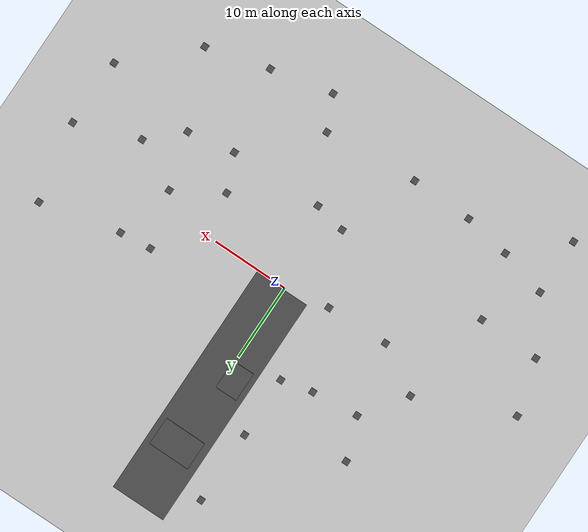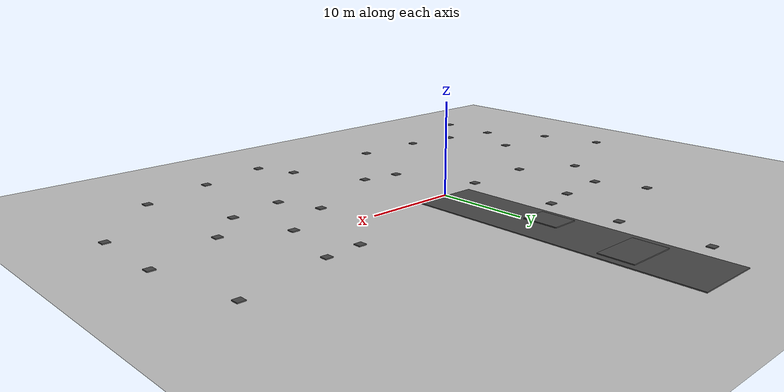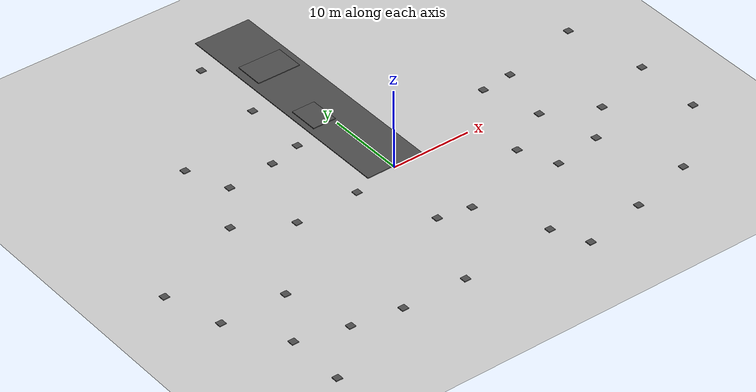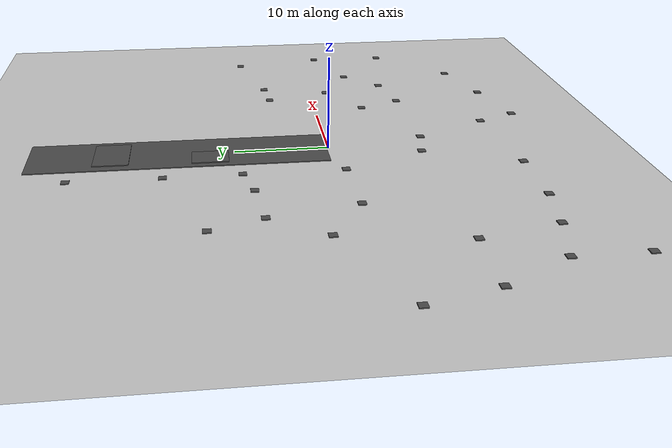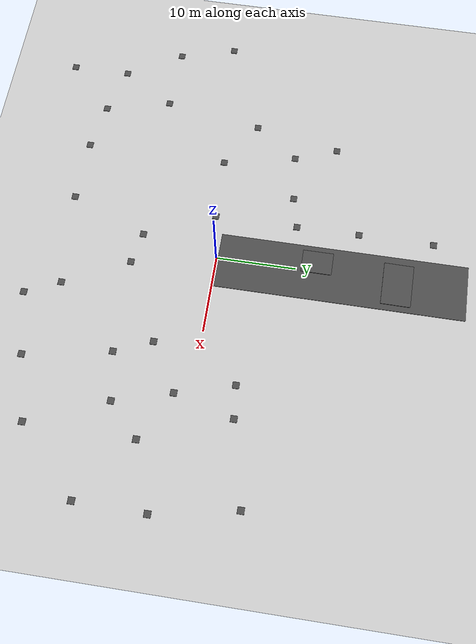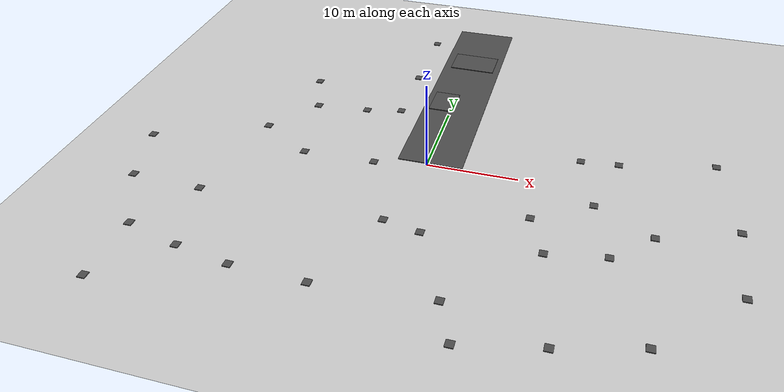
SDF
<sdf version="1.6">
 <world name="default">
  <light name="sun" type="directional">
   <pose>0 0 10 0 -0 0</pose>
   <diffuse>0.8 0.8 0.8 1</diffuse>
   <specular>0.2 0.2 0.2 1</specular>
   <attenuation>
    <range>1000</range>
    <constant>0.9</constant>
    <linear>0.01</linear>
    <quadratic>0.001</quadratic>
   </attenuation>
   <direction>-0.5 0.1 -0.9</direction>
  </light>
  <plugin name="ros_interface_plugin" filename="librotors_gazebo_ros_interface_plugin.so"/>
  <model name="ground_plane">
   <static>1</static>
   <link name="link">
    <collision name="collision">
     <geometry><plane><normal>0 0 1</normal><size>100 100</size></plane></geometry>
     <surface><friction><ode><mu>100</mu><mu2>50</mu2></ode></friction></surface>
    </collision>
    <visual name="visual">
     <cast_shadows>0</cast_shadows>
     <geometry><plane><normal>0 0 1</normal><size>100 100</size></plane></geometry>
     <material>
      <script><uri>file://media/materials/scripts/gazebo.material</uri><name>Gazebo/Grey</name></script>
     </material>
    </visual>
   </link>
  </model>
  <gravity>0 0 -9.8</gravity>
  <magnetic_field>6e-06 2.3e-05 -4.2e-05</magnetic_field>
  <atmosphere type="adiabatic"/>
  <physics name="default_physics" default="0" type="ode">
   <max_step_size>0.001</max_step_size>
   <real_time_factor>1</real_time_factor>
   <real_time_update_rate>1000</real_time_update_rate>
  </physics>
  <scene><ambient>0.4 0.4 0.4 1</ambient><background>0.7 0.7 0.7 1</background><shadows>1</shadows></scene>
  <spherical_coordinates>
   <surface_model>EARTH_WGS84</surface_model>
   <latitude_deg>0</latitude_deg>
   <longitude_deg>0</longitude_deg>
   <elevation>0</elevation>
   <heading_deg>0</heading_deg>
  </spherical_coordinates>
  <model name="asphalt_plane_update3">
   <link name="link">
    <inertial>
     <inertia><ixx>0</ixx><ixy>0</ixy><ixz>0</ixz><iyy>0</iyy><iyz>0</iyz><izz>0</izz></inertia>
     <mass>0</mass>
    </inertial>
    <visual name="visual">
     <cast_shadows>0</cast_shadows>
     <geometry><box><size>31.1902 7.25075 0.1</size></box></geometry>
     <material>
      <script>
       <uri>model://asphalt_plane/materials/scripts</uri>
       <uri>model://asphalt_plane/materials/textures</uri>
       <name>vrc/asphalt</name>
      </script>
      <shader type="pixel"/>
     </material>
    </visual>
    <collision name="collision">
     <geometry><box><size>31.1902 7.25075 0.1</size></box></geometry>
     <surface>
      <friction>
       <ode><mu>1</mu><mu2>1</mu2><fdir1>0 0 0</fdir1><slip1>0</slip1><slip2>0</slip2></ode>
       <torsional>
        <coefficient>1</coefficient>
        <patch_radius>0</patch_radius>
        <surface_radius>0</surface_radius>
        <use_patch_radius>1</use_patch_radius>
        <ode><slip>0</slip></ode>
       </torsional>
      </friction>
      <bounce><restitution_coefficient>0</restitution_coefficient><threshold>1e+06</threshold></bounce>
      <contact>
       <collide_without_contact>0</collide_without_contact>
       <collide_without_contact_bitmask>1</collide_without_contact_bitmask>
       <collide_bitmask>1</collide_bitmask>
       <ode>
        <soft_cfm>0</soft_cfm>
        <soft_erp>0.2</soft_erp>
        <kp>1e+13</kp>
        <kd>1</kd>
        <max_vel>0.01</max_vel>
        <min_depth>0</min_depth>
       </ode>
       <bullet>
        <split_impulse>1</split_impulse>
        <split_impulse_penetration_threshold>-0.01</split_impulse_penetration_threshold>
        <soft_cfm>0</soft_cfm>
        <soft_erp>0.2</soft_erp>
        <kp>1e+13</kp>
        <kd>1</kd>
       </bullet>
      </contact>
     </surface>
    </collision>
   </link>
   <static>1</static>
   <pose>0.251899 15.8038 0 0.004648 -0.000195 -1.57</pose>
  </model>
  <model name="asphalt_plane_updateblue_clone">
   <link name="link">
    <inertial>
     <inertia><ixx>0</ixx><ixy>0</ixy><ixz>0</ixz><iyy>0</iyy><iyz>0</iyz><izz>0</izz></inertia>
     <mass>0</mass>
    </inertial>
    <visual name="visual">
     <cast_shadows>0</cast_shadows>
     <geometry><box><size>0.821257 0.814438 0.1</size></box></geometry>
     <material>
      <script>
       <uri>model://asphalt_plane/materials/scripts</uri>
       <uri>model://asphalt_plane/materials/textures</uri>
       <name>vrc/asphalt</name>
      </script>
      <shader type="pixel"><normal_map>__default__</normal_map></shader>
      <ambient>0 1 1 1</ambient>
      <diffuse>0 1 1 1</diffuse>
      <specular>0 1 1 1</specular>
      <emissive>0 0 0 1</emissive>
     </material>
    </visual>
    <collision name="collision">
     <geometry><box><size>0.821257 0.814438 0.1</size></box></geometry>
     <surface>
      <friction>
       <ode><mu>1</mu><mu2>1</mu2><fdir1>0 0 0</fdir1><slip1>0</slip1><slip2>0</slip2></ode>
       <torsional>
        <coefficient>1</coefficient>
        <patch_radius>0</patch_radius>
        <surface_radius>0</surface_radius>
        <use_patch_radius>1</use_patch_radius>
        <ode><slip>0</slip></ode>
       </torsional>
      </friction>
      <bounce><restitution_coefficient>0</restitution_coefficient><threshold>1e+06</threshold></bounce>
      <contact>
       <collide_without_contact>0</collide_without_contact>
       <collide_without_contact_bitmask>1</collide_without_contact_bitmask>
       <collide_bitmask>1</collide_bitmask>
       <ode>
        <soft_cfm>0</soft_cfm>
        <soft_erp>0.2</soft_erp>
        <kp>1e+13</kp>
        <kd>1</kd>
        <max_vel>0.01</max_vel>
        <min_depth>0</min_depth>
       </ode>
       <bullet>
        <split_impulse>1</split_impulse>
        <split_impulse_penetration_threshold>-0.01</split_impulse_penetration_threshold>
        <soft_cfm>0</soft_cfm>
        <soft_erp>0.2</soft_erp>
        <kp>1e+13</kp>
        <kd>1</kd>
       </bullet>
      </contact>
     </surface>
    </collision>
   </link>
   <static>1</static>
   <pose>-5.85979 26.859 0 0 -0 0</pose>
  </model>
  <model name="asphalt_plane_updateblue_clone_clone_clone">
   <link name="link">
    <inertial>
     <inertia><ixx>0</ixx><ixy>0</ixy><ixz>0</ixz><iyy>0</iyy><iyz>0</iyz><izz>0</izz></inertia>
     <mass>0</mass>
    </inertial>
    <visual name="visual">
     <cast_shadows>0</cast_shadows>
     <geometry><box><size>2.93785 3.83992 0.1</size></box></geometry>
     <material>
      <script>
       <uri>model://asphalt_plane/materials/scripts</uri>
       <uri>model://asphalt_plane/materials/textures</uri>
       <name>vrc/asphalt</name>
      </script>
      <shader type="pixel"><normal_map>__default__</normal_map></shader>
      <ambient>0.776 0.769 0.765 1</ambient>
      <diffuse>0.773 0.769 0.765 1</diffuse>
      <specular>0.773 0.769 0.765 1</specular>
      <emissive>0.773 0.769 0.765 1</emissive>
     </material>
    </visual>
    <collision name="collision">
     <geometry><box><size>2.93785 3.83992 0.1</size></box></geometry>
     <surface>
      <friction>
       <ode><mu>1</mu><mu2>1</mu2><fdir1>0 0 0</fdir1><slip1>0</slip1><slip2>0</slip2></ode>
       <torsional>
        <coefficient>1</coefficient>
        <patch_radius>0</patch_radius>
        <surface_radius>0</surface_radius>
        <use_patch_radius>1</use_patch_radius>
        <ode><slip>0</slip></ode>
       </torsional>
      </friction>
      <bounce><restitution_coefficient>0</restitution_coefficient><threshold>1e+06</threshold></bounce>
      <contact>
       <collide_without_contact>0</collide_without_contact>
       <collide_without_contact_bitmask>1</collide_without_contact_bitmask>
       <collide_bitmask>1</collide_bitmask>
       <ode>
        <soft_cfm>0</soft_cfm>
        <soft_erp>0.2</soft_erp>
        <kp>1e+13</kp>
        <kd>1</kd>
        <max_vel>0.01</max_vel>
        <min_depth>0</min_depth>
       </ode>
       <bullet>
        <split_impulse>1</split_impulse>
        <split_impulse_penetration_threshold>-0.01</split_impulse_penetration_threshold>
        <soft_cfm>0</soft_cfm>
        <soft_erp>0.2</soft_erp>
        <kp>1e+13</kp>
        <kd>1</kd>
       </bullet>
      </contact>
     </surface>
    </collision>
   </link>
   <static>1</static>
   <pose>-1.21261 12.6004 0.1 0 -0 0</pose>
  </model>
  <model name="asphalt_plane_updateblue_clone_clone_clone_clone">
   <link name="link">
    <inertial>
     <inertia><ixx>0</ixx><ixy>0</ixy><ixz>0</ixz><iyy>0</iyy><iyz>0</iyz><izz>0</izz></inertia>
     <mass>0</mass>
    </inertial>
    <visual name="visual">
     <cast_shadows>0</cast_shadows>
     <geometry><box><size>3.69865 5.53696 0.1</size></box></geometry>
     <material>
      <script>
       <uri>model://asphalt_plane/materials/scripts</uri>
       <uri>model://asphalt_plane/materials/textures</uri>
       <name>vrc/asphalt</name>
      </script>
      <shader type="pixel"><normal_map>__default__</normal_map></shader>
      <ambient>0.776 0.769 0.765 1</ambient>
      <diffuse>0.773 0.769 0.765 1</diffuse>
      <specular>0.773 0.769 0.765 1</specular>
      <emissive>0.773 0.769 0.765 1</emissive>
     </material>
    </visual>
    <collision name="collision">
     <geometry><box><size>3.69865 5.53696 0.1</size></box></geometry>
     <surface>
      <friction>
       <ode><mu>1</mu><mu2>1</mu2><fdir1>0 0 0</fdir1><slip1>0</slip1><slip2>0</slip2></ode>
       <torsional>
        <coefficient>1</coefficient>
        <patch_radius>0</patch_radius>
        <surface_radius>0</surface_radius>
        <use_patch_radius>1</use_patch_radius>
        <ode><slip>0</slip></ode>
       </torsional>
      </friction>
      <bounce><restitution_coefficient>0</restitution_coefficient><threshold>1e+06</threshold></bounce>
      <contact>
       <collide_without_contact>0</collide_without_contact>
       <collide_without_contact_bitmask>1</collide_without_contact_bitmask>
       <collide_bitmask>1</collide_bitmask>
       <ode>
        <soft_cfm>0</soft_cfm>
        <soft_erp>0.2</soft_erp>
        <kp>1e+13</kp>
        <kd>1</kd>
        <max_vel>0.01</max_vel>
        <min_depth>0</min_depth>
       </ode>
       <bullet>
        <split_impulse>1</split_impulse>
        <split_impulse_penetration_threshold>-0.01</split_impulse_penetration_threshold>
        <soft_cfm>0</soft_cfm>
        <soft_erp>0.2</soft_erp>
        <kp>1e+13</kp>
        <kd>1</kd>
       </bullet>
      </contact>
     </surface>
    </collision>
   </link>
   <static>1</static>
   <pose>0.337939 22.7775 0.1 0 0 -1.57683</pose>
  </model>
  <model name="asphalt_plane_updateblue_clone_clone">
   <link name="link">
    <inertial>
     <inertia><ixx>0</ixx><ixy>0</ixy><ixz>0</ixz><iyy>0</iyy><iyz>0</iyz><izz>0</izz></inertia>
     <mass>0</mass>
    </inertial>
    <visual name="visual">
     <cast_shadows>0</cast_shadows>
     <geometry><box><size>0.821257 0.814438 0.1</size></box></geometry>
     <material>
      <script>
       <uri>model://asphalt_plane/materials/scripts</uri>
       <uri>model://asphalt_plane/materials/textures</uri>
       <name>vrc/asphalt</name>
      </script>
      <shader type="pixel"><normal_map>__default__</normal_map></shader>
      <ambient>0 1 1 1</ambient>
      <diffuse>0 1 1 1</diffuse>
      <specular>0 1 1 1</specular>
      <emissive>0 0 0 1</emissive>
     </material>
    </visual>
    <collision name="collision">
     <geometry><box><size>0.821257 0.814438 0.1</size></box></geometry>
     <surface>
      <friction>
       <ode><mu>1</mu><mu2>1</mu2><fdir1>0 0 0</fdir1><slip1>0</slip1><slip2>0</slip2></ode>
       <torsional>
        <coefficient>1</coefficient>
        <patch_radius>0</patch_radius>
        <surface_radius>0</surface_radius>
        <use_patch_radius>1</use_patch_radius>
        <ode><slip>0</slip></ode>
       </torsional>
      </friction>
      <bounce><restitution_coefficient>0</restitution_coefficient><threshold>1e+06</threshold></bounce>
      <contact>
       <collide_without_contact>0</collide_without_contact>
       <collide_without_contact_bitmask>1</collide_without_contact_bitmask>
       <collide_bitmask>1</collide_bitmask>
       <ode>
        <soft_cfm>0</soft_cfm>
        <soft_erp>0.2</soft_erp>
        <kp>1e+13</kp>
        <kd>1</kd>
        <max_vel>0.01</max_vel>
        <min_depth>0</min_depth>
       </ode>
       <bullet>
        <split_impulse>1</split_impulse>
        <split_impulse_penetration_threshold>-0.01</split_impulse_penetration_threshold>
        <soft_cfm>0</soft_cfm>
        <soft_erp>0.2</soft_erp>
        <kp>1e+13</kp>
        <kd>1</kd>
       </bullet>
      </contact>
     </surface>
    </collision>
   </link>
   <static>1</static>
   <pose>-5.8573 17.3974 0 0 -0 0</pose>
  </model>
  <model name="asphalt_plane_updateblue_clone_clone_0">
   <link name="link">
    <inertial>
     <inertia><ixx>0</ixx><ixy>0</ixy><ixz>0</ixz><iyy>0</iyy><iyz>0</iyz><izz>0</izz></inertia>
     <mass>0</mass>
    </inertial>
    <visual name="visual">
     <cast_shadows>0</cast_shadows>
     <geometry><box><size>0.821257 0.814438 0.1</size></box></geometry>
     <material>
      <script>
       <uri>model://asphalt_plane/materials/scripts</uri>
       <uri>model://asphalt_plane/materials/textures</uri>
       <name>vrc/asphalt</name>
      </script>
      <shader type="pixel"><normal_map>__default__</normal_map></shader>
      <ambient>0 1 1 1</ambient>
      <diffuse>0 1 1 1</diffuse>
      <specular>0 1 1 1</specular>
      <emissive>0 0 0 1</emissive>
     </material>
    </visual>
    <collision name="collision">
     <geometry><box><size>0.821257 0.814438 0.1</size></box></geometry>
     <surface>
      <friction>
       <ode><mu>1</mu><mu2>1</mu2><fdir1>0 0 0</fdir1><slip1>0</slip1><slip2>0</slip2></ode>
       <torsional>
        <coefficient>1</coefficient>
        <patch_radius>0</patch_radius>
        <surface_radius>0</surface_radius>
        <use_patch_radius>1</use_patch_radius>
        <ode><slip>0</slip></ode>
       </torsional>
      </friction>
      <bounce><restitution_coefficient>0</restitution_coefficient><threshold>1e+06</threshold></bounce>
      <contact>
       <collide_without_contact>0</collide_without_contact>
       <collide_without_contact_bitmask>1</collide_without_contact_bitmask>
       <collide_bitmask>1</collide_bitmask>
       <ode>
        <soft_cfm>0</soft_cfm>
        <soft_erp>0.2</soft_erp>
        <kp>1e+13</kp>
        <kd>1</kd>
        <max_vel>0.01</max_vel>
        <min_depth>0</min_depth>
       </ode>
       <bullet>
        <split_impulse>1</split_impulse>
        <split_impulse_penetration_threshold>-0.01</split_impulse_penetration_threshold>
        <soft_cfm>0</soft_cfm>
        <soft_erp>0.2</soft_erp>
        <kp>1e+13</kp>
        <kd>1</kd>
       </bullet>
      </contact>
     </surface>
    </collision>
   </link>
   <static>1</static>
   <pose>-5.7888 9.45481 0 0 -0 0</pose>
  </model>
  <model name="asphalt_plane_updateblue_clone_clone_1">
   <link name="link">
    <inertial>
     <inertia><ixx>0</ixx><ixy>0</ixy><ixz>0</ixz><iyy>0</iyy><iyz>0</iyz><izz>0</izz></inertia>
     <mass>0</mass>
    </inertial>
    <visual name="visual">
     <cast_shadows>0</cast_shadows>
     <geometry><box><size>0.821257 0.814438 0.1</size></box></geometry>
     <material>
      <script>
       <uri>model://asphalt_plane/materials/scripts</uri>
       <uri>model://asphalt_plane/materials/textures</uri>
       <name>vrc/asphalt</name>
      </script>
      <shader type="pixel"><normal_map>__default__</normal_map></shader>
      <ambient>0 1 1 1</ambient>
      <diffuse>0 1 1 1</diffuse>
      <specular>0 1 1 1</specular>
      <emissive>0 0 0 1</emissive>
     </material>
    </visual>
    <collision name="collision">
     <geometry><box><size>0.821257 0.814438 0.1</size></box></geometry>
     <surface>
      <friction>
       <ode><mu>1</mu><mu2>1</mu2><fdir1>0 0 0</fdir1><slip1>0</slip1><slip2>0</slip2></ode>
       <torsional>
        <coefficient>1</coefficient>
        <patch_radius>0</patch_radius>
        <surface_radius>0</surface_radius>
        <use_patch_radius>1</use_patch_radius>
        <ode><slip>0</slip></ode>
       </torsional>
      </friction>
      <bounce><restitution_coefficient>0</restitution_coefficient><threshold>1e+06</threshold></bounce>
      <contact>
       <collide_without_contact>0</collide_without_contact>
       <collide_without_contact_bitmask>1</collide_without_contact_bitmask>
       <collide_bitmask>1</collide_bitmask>
       <ode>
        <soft_cfm>0</soft_cfm>
        <soft_erp>0.2</soft_erp>
        <kp>1e+13</kp>
        <kd>1</kd>
        <max_vel>0.01</max_vel>
        <min_depth>0</min_depth>
       </ode>
       <bullet>
        <split_impulse>1</split_impulse>
        <split_impulse_penetration_threshold>-0.01</split_impulse_penetration_threshold>
        <soft_cfm>0</soft_cfm>
        <soft_erp>0.2</soft_erp>
        <kp>1e+13</kp>
        <kd>1</kd>
       </bullet>
      </contact>
     </surface>
    </collision>
   </link>
   <static>1</static>
   <pose>-5.75754 -1.01326 0 0 -0 0</pose>
  </model>
  <model name="asphalt_plane_updateblue_clone_clone_2">
   <link name="link">
    <inertial>
     <inertia><ixx>0</ixx><ixy>0</ixy><ixz>0</ixz><iyy>0</iyy><iyz>0</iyz><izz>0</izz></inertia>
     <mass>0</mass>
    </inertial>
    <visual name="visual">
     <cast_shadows>0</cast_shadows>
     <geometry><box><size>0.821257 0.814438 0.1</size></box></geometry>
     <material>
      <script>
       <uri>model://asphalt_plane/materials/scripts</uri>
       <uri>model://asphalt_plane/materials/textures</uri>
       <name>vrc/asphalt</name>
      </script>
      <shader type="pixel"><normal_map>__default__</normal_map></shader>
      <ambient>0 1 1 1</ambient>
      <diffuse>0 1 1 1</diffuse>
      <specular>0 1 1 1</specular>
      <emissive>0 0 0 1</emissive>
     </material>
    </visual>
    <collision name="collision">
     <geometry><box><size>0.821257 0.814438 0.1</size></box></geometry>
     <surface>
      <friction>
       <ode><mu>1</mu><mu2>1</mu2><fdir1>0 0 0</fdir1><slip1>0</slip1><slip2>0</slip2></ode>
       <torsional>
        <coefficient>1</coefficient>
        <patch_radius>0</patch_radius>
        <surface_radius>0</surface_radius>
        <use_patch_radius>1</use_patch_radius>
        <ode><slip>0</slip></ode>
       </torsional>
      </friction>
      <bounce><restitution_coefficient>0</restitution_coefficient><threshold>1e+06</threshold></bounce>
      <contact>
       <collide_without_contact>0</collide_without_contact>
       <collide_without_contact_bitmask>1</collide_without_contact_bitmask>
       <collide_bitmask>1</collide_bitmask>
       <ode>
        <soft_cfm>0</soft_cfm>
        <soft_erp>0.2</soft_erp>
        <kp>1e+13</kp>
        <kd>1</kd>
        <max_vel>0.01</max_vel>
        <min_depth>0</min_depth>
       </ode>
       <bullet>
        <split_impulse>1</split_impulse>
        <split_impulse_penetration_threshold>-0.01</split_impulse_penetration_threshold>
        <soft_cfm>0</soft_cfm>
        <soft_erp>0.2</soft_erp>
        <kp>1e+13</kp>
        <kd>1</kd>
       </bullet>
      </contact>
     </surface>
    </collision>
   </link>
   <static>1</static>
   <pose>-9.8052 8.51299 0 0 -0 0</pose>
  </model>
  <model name="asphalt_plane_updateblue_clone_clone_3">
   <link name="link">
    <inertial>
     <inertia><ixx>0</ixx><ixy>0</ixy><ixz>0</ixz><iyy>0</iyy><iyz>0</iyz><izz>0</izz></inertia>
     <mass>0</mass>
    </inertial>
    <visual name="visual">
     <cast_shadows>0</cast_shadows>
     <geometry><box><size>0.821257 0.814438 0.1</size></box></geometry>
     <material>
      <script>
       <uri>model://asphalt_plane/materials/scripts</uri>
       <uri>model://asphalt_plane/materials/textures</uri>
       <name>vrc/asphalt</name>
      </script>
      <shader type="pixel"><normal_map>__default__</normal_map></shader>
      <ambient>0 1 1 1</ambient>
      <diffuse>0 1 1 1</diffuse>
      <specular>0 1 1 1</specular>
      <emissive>0 0 0 1</emissive>
     </material>
    </visual>
    <collision name="collision">
     <geometry><box><size>0.821257 0.814438 0.1</size></box></geometry>
     <surface>
      <friction>
       <ode><mu>1</mu><mu2>1</mu2><fdir1>0 0 0</fdir1><slip1>0</slip1><slip2>0</slip2></ode>
       <torsional>
        <coefficient>1</coefficient>
        <patch_radius>0</patch_radius>
        <surface_radius>0</surface_radius>
        <use_patch_radius>1</use_patch_radius>
        <ode><slip>0</slip></ode>
       </torsional>
      </friction>
      <bounce><restitution_coefficient>0</restitution_coefficient><threshold>1e+06</threshold></bounce>
      <contact>
       <collide_without_contact>0</collide_without_contact>
       <collide_without_contact_bitmask>1</collide_without_contact_bitmask>
       <collide_bitmask>1</collide_bitmask>
       <ode>
        <soft_cfm>0</soft_cfm>
        <soft_erp>0.2</soft_erp>
        <kp>1e+13</kp>
        <kd>1</kd>
        <max_vel>0.01</max_vel>
        <min_depth>0</min_depth>
       </ode>
       <bullet>
        <split_impulse>1</split_impulse>
        <split_impulse_penetration_threshold>-0.01</split_impulse_penetration_threshold>
        <soft_cfm>0</soft_cfm>
        <soft_erp>0.2</soft_erp>
        <kp>1e+13</kp>
        <kd>1</kd>
       </bullet>
      </contact>
     </surface>
    </collision>
   </link>
   <static>1</static>
   <pose>-15.8321 7.91363 0 0 -0 0</pose>
  </model>
  <model name="asphalt_plane_updateblue_clone_clone_4">
   <link name="link">
    <inertial>
     <inertia><ixx>0</ixx><ixy>0</ixy><ixz>0</ixz><iyy>0</iyy><iyz>0</iyz><izz>0</izz></inertia>
     <mass>0</mass>
    </inertial>
    <visual name="visual">
     <cast_shadows>0</cast_shadows>
     <geometry><box><size>0.821257 0.814438 0.1</size></box></geometry>
     <material>
      <script>
       <uri>model://asphalt_plane/materials/scripts</uri>
       <uri>model://asphalt_plane/materials/textures</uri>
       <name>vrc/asphalt</name>
      </script>
      <shader type="pixel"><normal_map>__default__</normal_map></shader>
      <ambient>0 1 1 1</ambient>
      <diffuse>0 1 1 1</diffuse>
      <specular>0 1 1 1</specular>
      <emissive>0 0 0 1</emissive>
     </material>
    </visual>
    <collision name="collision">
     <geometry><box><size>0.821257 0.814438 0.1</size></box></geometry>
     <surface>
      <friction>
       <ode><mu>1</mu><mu2>1</mu2><fdir1>0 0 0</fdir1><slip1>0</slip1><slip2>0</slip2></ode>
       <torsional>
        <coefficient>1</coefficient>
        <patch_radius>0</patch_radius>
        <surface_radius>0</surface_radius>
        <use_patch_radius>1</use_patch_radius>
        <ode><slip>0</slip></ode>
       </torsional>
      </friction>
      <bounce><restitution_coefficient>0</restitution_coefficient><threshold>1e+06</threshold></bounce>
      <contact>
       <collide_without_contact>0</collide_without_contact>
       <collide_without_contact_bitmask>1</collide_without_contact_bitmask>
       <collide_bitmask>1</collide_bitmask>
       <ode>
        <soft_cfm>0</soft_cfm>
        <soft_erp>0.2</soft_erp>
        <kp>1e+13</kp>
        <kd>1</kd>
        <max_vel>0.01</max_vel>
        <min_depth>0</min_depth>
       </ode>
       <bullet>
        <split_impulse>1</split_impulse>
        <split_impulse_penetration_threshold>-0.01</split_impulse_penetration_threshold>
        <soft_cfm>0</soft_cfm>
        <soft_erp>0.2</soft_erp>
        <kp>1e+13</kp>
        <kd>1</kd>
       </bullet>
      </contact>
     </surface>
    </collision>
   </link>
   <static>1</static>
   <pose>-17.8167 13.2316 0 0 -0 0</pose>
  </model>
  <model name="asphalt_plane_updateblue_clone_clone_5">
   <link name="link">
    <inertial>
     <inertia><ixx>0</ixx><ixy>0</ixy><ixz>0</ixz><iyy>0</iyy><iyz>0</iyz><izz>0</izz></inertia>
     <mass>0</mass>
    </inertial>
    <visual name="visual">
     <cast_shadows>0</cast_shadows>
     <geometry><box><size>0.821257 0.814438 0.1</size></box></geometry>
     <material>
      <script>
       <uri>model://asphalt_plane/materials/scripts</uri>
       <uri>model://asphalt_plane/materials/textures</uri>
       <name>vrc/asphalt</name>
      </script>
      <shader type="pixel"><normal_map>__default__</normal_map></shader>
      <ambient>0 1 1 1</ambient>
      <diffuse>0 1 1 1</diffuse>
      <specular>0 1 1 1</specular>
      <emissive>0 0 0 1</emissive>
     </material>
    </visual>
    <collision name="collision">
     <geometry><box><size>0.821257 0.814438 0.1</size></box></geometry>
     <surface>
      <friction>
       <ode><mu>1</mu><mu2>1</mu2><fdir1>0 0 0</fdir1><slip1>0</slip1><slip2>0</slip2></ode>
       <torsional>
        <coefficient>1</coefficient>
        <patch_radius>0</patch_radius>
        <surface_radius>0</surface_radius>
        <use_patch_radius>1</use_patch_radius>
        <ode><slip>0</slip></ode>
       </torsional>
      </friction>
      <bounce><restitution_coefficient>0</restitution_coefficient><threshold>1e+06</threshold></bounce>
      <contact>
       <collide_without_contact>0</collide_without_contact>
       <collide_without_contact_bitmask>1</collide_without_contact_bitmask>
       <collide_bitmask>1</collide_bitmask>
       <ode>
        <soft_cfm>0</soft_cfm>
        <soft_erp>0.2</soft_erp>
        <kp>1e+13</kp>
        <kd>1</kd>
        <max_vel>0.01</max_vel>
        <min_depth>0</min_depth>
       </ode>
       <bullet>
        <split_impulse>1</split_impulse>
        <split_impulse_penetration_threshold>-0.01</split_impulse_penetration_threshold>
        <soft_cfm>0</soft_cfm>
        <soft_erp>0.2</soft_erp>
        <kp>1e+13</kp>
        <kd>1</kd>
       </bullet>
      </contact>
     </surface>
    </collision>
   </link>
   <static>1</static>
   <pose>-13.8166 -1.25605 0 0 -0 0</pose>
  </model>
  <model name="asphalt_plane_updateblue_clone_clone_6">
   <link name="link">
    <inertial>
     <inertia><ixx>0</ixx><ixy>0</ixy><ixz>0</ixz><iyy>0</iyy><iyz>0</iyz><izz>0</izz></inertia>
     <mass>0</mass>
    </inertial>
    <visual name="visual">
     <cast_shadows>0</cast_shadows>
     <geometry><box><size>0.821257 0.814438 0.1</size></box></geometry>
     <material>
      <script>
       <uri>model://asphalt_plane/materials/scripts</uri>
       <uri>model://asphalt_plane/materials/textures</uri>
       <name>vrc/asphalt</name>
      </script>
      <shader type="pixel"><normal_map>__default__</normal_map></shader>
      <ambient>0 1 1 1</ambient>
      <diffuse>0 1 1 1</diffuse>
      <specular>0 1 1 1</specular>
      <emissive>0 0 0 1</emissive>
     </material>
    </visual>
    <collision name="collision">
     <geometry><box><size>0.821257 0.814438 0.1</size></box></geometry>
     <surface>
      <friction>
       <ode><mu>1</mu><mu2>1</mu2><fdir1>0 0 0</fdir1><slip1>0</slip1><slip2>0</slip2></ode>
       <torsional>
        <coefficient>1</coefficient>
        <patch_radius>0</patch_radius>
        <surface_radius>0</surface_radius>
        <use_patch_radius>1</use_patch_radius>
        <ode><slip>0</slip></ode>
       </torsional>
      </friction>
      <bounce><restitution_coefficient>0</restitution_coefficient><threshold>1e+06</threshold></bounce>
      <contact>
       <collide_without_contact>0</collide_without_contact>
       <collide_without_contact_bitmask>1</collide_without_contact_bitmask>
       <collide_bitmask>1</collide_bitmask>
       <ode>
        <soft_cfm>0</soft_cfm>
        <soft_erp>0.2</soft_erp>
        <kp>1e+13</kp>
        <kd>1</kd>
        <max_vel>0.01</max_vel>
        <min_depth>0</min_depth>
       </ode>
       <bullet>
        <split_impulse>1</split_impulse>
        <split_impulse_penetration_threshold>-0.01</split_impulse_penetration_threshold>
        <soft_cfm>0</soft_cfm>
        <soft_erp>0.2</soft_erp>
        <kp>1e+13</kp>
        <kd>1</kd>
       </bullet>
      </contact>
     </surface>
    </collision>
   </link>
   <static>1</static>
   <pose>-19.8487 2.34552 0 0 -0 0</pose>
  </model>
  <model name="asphalt_plane_updateblue_clone_clone_7">
   <link name="link">
    <inertial>
     <inertia><ixx>0</ixx><ixy>0</ixy><ixz>0</ixz><iyy>0</iyy><iyz>0</iyz><izz>0</izz></inertia>
     <mass>0</mass>
    </inertial>
    <visual name="visual">
     <cast_shadows>0</cast_shadows>
     <geometry><box><size>0.821257 0.814438 0.1</size></box></geometry>
     <material>
      <script>
       <uri>model://asphalt_plane/materials/scripts</uri>
       <uri>model://asphalt_plane/materials/textures</uri>
       <name>vrc/asphalt</name>
      </script>
      <shader type="pixel"><normal_map>__default__</normal_map></shader>
      <ambient>0 1 1 1</ambient>
      <diffuse>0 1 1 1</diffuse>
      <specular>0 1 1 1</specular>
      <emissive>0 0 0 1</emissive>
     </material>
    </visual>
    <collision name="collision">
     <geometry><box><size>0.821257 0.814438 0.1</size></box></geometry>
     <surface>
      <friction>
       <ode><mu>1</mu><mu2>1</mu2><fdir1>0 0 0</fdir1><slip1>0</slip1><slip2>0</slip2></ode>
       <torsional>
        <coefficient>1</coefficient>
        <patch_radius>0</patch_radius>
        <surface_radius>0</surface_radius>
        <use_patch_radius>1</use_patch_radius>
        <ode><slip>0</slip></ode>
       </torsional>
      </friction>
      <bounce><restitution_coefficient>0</restitution_coefficient><threshold>1e+06</threshold></bounce>
      <contact>
       <collide_without_contact>0</collide_without_contact>
       <collide_without_contact_bitmask>1</collide_without_contact_bitmask>
       <collide_bitmask>1</collide_bitmask>
       <ode>
        <soft_cfm>0</soft_cfm>
        <soft_erp>0.2</soft_erp>
        <kp>1e+13</kp>
        <kd>1</kd>
        <max_vel>0.01</max_vel>
        <min_depth>0</min_depth>
       </ode>
       <bullet>
        <split_impulse>1</split_impulse>
        <split_impulse_penetration_threshold>-0.01</split_impulse_penetration_threshold>
        <soft_cfm>0</soft_cfm>
        <soft_erp>0.2</soft_erp>
        <kp>1e+13</kp>
        <kd>1</kd>
       </bullet>
      </contact>
     </surface>
    </collision>
   </link>
   <static>1</static>
   <pose>-19.8055 -18.3183 0 0 -0 0</pose>
  </model>
  <model name="asphalt_plane_updateblue_clone_clone_8">
   <link name="link">
    <inertial>
     <inertia><ixx>0</ixx><ixy>0</ixy><ixz>0</ixz><iyy>0</iyy><iyz>0</iyz><izz>0</izz></inertia>
     <mass>0</mass>
    </inertial>
    <visual name="visual">
     <cast_shadows>0</cast_shadows>
     <geometry><box><size>0.821257 0.814438 0.1</size></box></geometry>
     <material>
      <script>
       <uri>model://asphalt_plane/materials/scripts</uri>
       <uri>model://asphalt_plane/materials/textures</uri>
       <name>vrc/asphalt</name>
      </script>
      <shader type="pixel"><normal_map>__default__</normal_map></shader>
      <ambient>0 1 1 1</ambient>
      <diffuse>0 1 1 1</diffuse>
      <specular>0 1 1 1</specular>
      <emissive>0 0 0 1</emissive>
     </material>
    </visual>
    <collision name="collision">
     <geometry><box><size>0.821257 0.814438 0.1</size></box></geometry>
     <surface>
      <friction>
       <ode><mu>1</mu><mu2>1</mu2><fdir1>0 0 0</fdir1><slip1>0</slip1><slip2>0</slip2></ode>
       <torsional>
        <coefficient>1</coefficient>
        <patch_radius>0</patch_radius>
        <surface_radius>0</surface_radius>
        <use_patch_radius>1</use_patch_radius>
        <ode><slip>0</slip></ode>
       </torsional>
      </friction>
      <bounce><restitution_coefficient>0</restitution_coefficient><threshold>1e+06</threshold></bounce>
      <contact>
       <collide_without_contact>0</collide_without_contact>
       <collide_without_contact_bitmask>1</collide_without_contact_bitmask>
       <collide_bitmask>1</collide_bitmask>
       <ode>
        <soft_cfm>0</soft_cfm>
        <soft_erp>0.2</soft_erp>
        <kp>1e+13</kp>
        <kd>1</kd>
        <max_vel>0.01</max_vel>
        <min_depth>0</min_depth>
       </ode>
       <bullet>
        <split_impulse>1</split_impulse>
        <split_impulse_penetration_threshold>-0.01</split_impulse_penetration_threshold>
        <soft_cfm>0</soft_cfm>
        <soft_erp>0.2</soft_erp>
        <kp>1e+13</kp>
        <kd>1</kd>
       </bullet>
      </contact>
     </surface>
    </collision>
   </link>
   <static>1</static>
   <pose>-21.8947 -10.0955 0 0 -0 0</pose>
  </model>
  <model name="asphalt_plane_updateblue_clone_clone_9">
   <link name="link">
    <inertial>
     <inertia><ixx>0</ixx><ixy>0</ixy><ixz>0</ixz><iyy>0</iyy><iyz>0</iyz><izz>0</izz></inertia>
     <mass>0</mass>
    </inertial>
    <visual name="visual">
     <cast_shadows>0</cast_shadows>
     <geometry><box><size>0.821257 0.814438 0.1</size></box></geometry>
     <material>
      <script>
       <uri>model://asphalt_plane/materials/scripts</uri>
       <uri>model://asphalt_plane/materials/textures</uri>
       <name>vrc/asphalt</name>
      </script>
      <shader type="pixel"><normal_map>__default__</normal_map></shader>
      <ambient>0 1 1 1</ambient>
      <diffuse>0 1 1 1</diffuse>
      <specular>0 1 1 1</specular>
      <emissive>0 0 0 1</emissive>
     </material>
    </visual>
    <collision name="collision">
     <geometry><box><size>0.821257 0.814438 0.1</size></box></geometry>
     <surface>
      <friction>
       <ode><mu>1</mu><mu2>1</mu2><fdir1>0 0 0</fdir1><slip1>0</slip1><slip2>0</slip2></ode>
       <torsional>
        <coefficient>1</coefficient>
        <patch_radius>0</patch_radius>
        <surface_radius>0</surface_radius>
        <use_patch_radius>1</use_patch_radius>
        <ode><slip>0</slip></ode>
       </torsional>
      </friction>
      <bounce><restitution_coefficient>0</restitution_coefficient><threshold>1e+06</threshold></bounce>
      <contact>
       <collide_without_contact>0</collide_without_contact>
       <collide_without_contact_bitmask>1</collide_without_contact_bitmask>
       <collide_bitmask>1</collide_bitmask>
       <ode>
        <soft_cfm>0</soft_cfm>
        <soft_erp>0.2</soft_erp>
        <kp>1e+13</kp>
        <kd>1</kd>
        <max_vel>0.01</max_vel>
        <min_depth>0</min_depth>
       </ode>
       <bullet>
        <split_impulse>1</split_impulse>
        <split_impulse_penetration_threshold>-0.01</split_impulse_penetration_threshold>
        <soft_cfm>0</soft_cfm>
        <soft_erp>0.2</soft_erp>
        <kp>1e+13</kp>
        <kd>1</kd>
       </bullet>
      </contact>
     </surface>
    </collision>
   </link>
   <static>1</static>
   <pose>-13.809 -19.328 0 0 -0 0</pose>
  </model>
  <model name="asphalt_plane_updateblue_clone_clone_10">
   <link name="link">
    <inertial>
     <inertia><ixx>0</ixx><ixy>0</ixy><ixz>0</ixz><iyy>0</iyy><iyz>0</iyz><izz>0</izz></inertia>
     <mass>0</mass>
    </inertial>
    <visual name="visual">
     <cast_shadows>0</cast_shadows>
     <geometry><box><size>0.821257 0.814438 0.1</size></box></geometry>
     <material>
      <script>
       <uri>model://asphalt_plane/materials/scripts</uri>
       <uri>model://asphalt_plane/materials/textures</uri>
       <name>vrc/asphalt</name>
      </script>
      <shader type="pixel"><normal_map>__default__</normal_map></shader>
      <ambient>0 1 1 1</ambient>
      <diffuse>0 1 1 1</diffuse>
      <specular>0 1 1 1</specular>
      <emissive>0 0 0 1</emissive>
     </material>
    </visual>
    <collision name="collision">
     <geometry><box><size>0.821257 0.814438 0.1</size></box></geometry>
     <surface>
      <friction>
       <ode><mu>1</mu><mu2>1</mu2><fdir1>0 0 0</fdir1><slip1>0</slip1><slip2>0</slip2></ode>
       <torsional>
        <coefficient>1</coefficient>
        <patch_radius>0</patch_radius>
        <surface_radius>0</surface_radius>
        <use_patch_radius>1</use_patch_radius>
        <ode><slip>0</slip></ode>
       </torsional>
      </friction>
      <bounce><restitution_coefficient>0</restitution_coefficient><threshold>1e+06</threshold></bounce>
      <contact>
       <collide_without_contact>0</collide_without_contact>
       <collide_without_contact_bitmask>1</collide_without_contact_bitmask>
       <collide_bitmask>1</collide_bitmask>
       <ode>
        <soft_cfm>0</soft_cfm>
        <soft_erp>0.2</soft_erp>
        <kp>1e+13</kp>
        <kd>1</kd>
        <max_vel>0.01</max_vel>
        <min_depth>0</min_depth>
       </ode>
       <bullet>
        <split_impulse>1</split_impulse>
        <split_impulse_penetration_threshold>-0.01</split_impulse_penetration_threshold>
        <soft_cfm>0</soft_cfm>
        <soft_erp>0.2</soft_erp>
        <kp>1e+13</kp>
        <kd>1</kd>
       </bullet>
      </contact>
     </surface>
    </collision>
   </link>
   <static>1</static>
   <pose>6.21493 -18.4834 0 0 -0 0</pose>
  </model>
  <model name="asphalt_plane_updateblue_clone_clone_11">
   <link name="link">
    <inertial>
     <inertia><ixx>0</ixx><ixy>0</ixy><ixz>0</ixz><iyy>0</iyy><iyz>0</iyz><izz>0</izz></inertia>
     <mass>0</mass>
    </inertial>
    <visual name="visual">
     <cast_shadows>0</cast_shadows>
     <geometry><box><size>0.821257 0.814438 0.1</size></box></geometry>
     <material>
      <script>
       <uri>model://asphalt_plane/materials/scripts</uri>
       <uri>model://asphalt_plane/materials/textures</uri>
       <name>vrc/asphalt</name>
      </script>
      <shader type="pixel"><normal_map>__default__</normal_map></shader>
      <ambient>0 1 1 1</ambient>
      <diffuse>0 1 1 1</diffuse>
      <specular>0 1 1 1</specular>
      <emissive>0 0 0 1</emissive>
     </material>
    </visual>
    <collision name="collision">
     <geometry><box><size>0.821257 0.814438 0.1</size></box></geometry>
     <surface>
      <friction>
       <ode><mu>1</mu><mu2>1</mu2><fdir1>0 0 0</fdir1><slip1>0</slip1><slip2>0</slip2></ode>
       <torsional>
        <coefficient>1</coefficient>
        <patch_radius>0</patch_radius>
        <surface_radius>0</surface_radius>
        <use_patch_radius>1</use_patch_radius>
        <ode><slip>0</slip></ode>
       </torsional>
      </friction>
      <bounce><restitution_coefficient>0</restitution_coefficient><threshold>1e+06</threshold></bounce>
      <contact>
       <collide_without_contact>0</collide_without_contact>
       <collide_without_contact_bitmask>1</collide_without_contact_bitmask>
       <collide_bitmask>1</collide_bitmask>
       <ode>
        <soft_cfm>0</soft_cfm>
        <soft_erp>0.2</soft_erp>
        <kp>1e+13</kp>
        <kd>1</kd>
        <max_vel>0.01</max_vel>
        <min_depth>0</min_depth>
       </ode>
       <bullet>
        <split_impulse>1</split_impulse>
        <split_impulse_penetration_threshold>-0.01</split_impulse_penetration_threshold>
        <soft_cfm>0</soft_cfm>
        <soft_erp>0.2</soft_erp>
        <kp>1e+13</kp>
        <kd>1</kd>
       </bullet>
      </contact>
     </surface>
    </collision>
   </link>
   <static>1</static>
   <pose>8.19247 -22.7764 0 0 -0 0</pose>
  </model>
  <model name="asphalt_plane_updateblue_clone_clone_12">
   <link name="link">
    <inertial>
     <inertia><ixx>0</ixx><ixy>0</ixy><ixz>0</ixz><iyy>0</iyy><iyz>0</iyz><izz>0</izz></inertia>
     <mass>0</mass>
    </inertial>
    <visual name="visual">
     <cast_shadows>0</cast_shadows>
     <geometry><box><size>0.821257 0.814438 0.1</size></box></geometry>
     <material>
      <script>
       <uri>model://asphalt_plane/materials/scripts</uri>
       <uri>model://asphalt_plane/materials/textures</uri>
       <name>vrc/asphalt</name>
      </script>
      <shader type="pixel"><normal_map>__default__</normal_map></shader>
      <ambient>0 1 1 1</ambient>
      <diffuse>0 1 1 1</diffuse>
      <specular>0 1 1 1</specular>
      <emissive>0 0 0 1</emissive>
     </material>
    </visual>
    <collision name="collision">
     <geometry><box><size>0.821257 0.814438 0.1</size></box></geometry>
     <surface>
      <friction>
       <ode><mu>1</mu><mu2>1</mu2><fdir1>0 0 0</fdir1><slip1>0</slip1><slip2>0</slip2></ode>
       <torsional>
        <coefficient>1</coefficient>
        <patch_radius>0</patch_radius>
        <surface_radius>0</surface_radius>
        <use_patch_radius>1</use_patch_radius>
        <ode><slip>0</slip></ode>
       </torsional>
      </friction>
      <bounce><restitution_coefficient>0</restitution_coefficient><threshold>1e+06</threshold></bounce>
      <contact>
       <collide_without_contact>0</collide_without_contact>
       <collide_without_contact_bitmask>1</collide_without_contact_bitmask>
       <collide_bitmask>1</collide_bitmask>
       <ode>
        <soft_cfm>0</soft_cfm>
        <soft_erp>0.2</soft_erp>
        <kp>1e+13</kp>
        <kd>1</kd>
        <max_vel>0.01</max_vel>
        <min_depth>0</min_depth>
       </ode>
       <bullet>
        <split_impulse>1</split_impulse>
        <split_impulse_penetration_threshold>-0.01</split_impulse_penetration_threshold>
        <soft_cfm>0</soft_cfm>
        <soft_erp>0.2</soft_erp>
        <kp>1e+13</kp>
        <kd>1</kd>
       </bullet>
      </contact>
     </surface>
    </collision>
   </link>
   <static>1</static>
   <pose>16.1417 -21.0274 0 0 -0 0</pose>
  </model>
  <model name="asphalt_plane_updateblue_clone_clone_13">
   <link name="link">
    <inertial>
     <inertia><ixx>0</ixx><ixy>0</ixy><ixz>0</ixz><iyy>0</iyy><iyz>0</iyz><izz>0</izz></inertia>
     <mass>0</mass>
    </inertial>
    <visual name="visual">
     <cast_shadows>0</cast_shadows>
     <geometry><box><size>0.821257 0.814438 0.1</size></box></geometry>
     <material>
      <script>
       <uri>model://asphalt_plane/materials/scripts</uri>
       <uri>model://asphalt_plane/materials/textures</uri>
       <name>vrc/asphalt</name>
      </script>
      <shader type="pixel"><normal_map>__default__</normal_map></shader>
      <ambient>0 1 1 1</ambient>
      <diffuse>0 1 1 1</diffuse>
      <specular>0 1 1 1</specular>
      <emissive>0 0 0 1</emissive>
     </material>
    </visual>
    <collision name="collision">
     <geometry><box><size>0.821257 0.814438 0.1</size></box></geometry>
     <surface>
      <friction>
       <ode><mu>1</mu><mu2>1</mu2><fdir1>0 0 0</fdir1><slip1>0</slip1><slip2>0</slip2></ode>
       <torsional>
        <coefficient>1</coefficient>
        <patch_radius>0</patch_radius>
        <surface_radius>0</surface_radius>
        <use_patch_radius>1</use_patch_radius>
        <ode><slip>0</slip></ode>
       </torsional>
      </friction>
      <bounce><restitution_coefficient>0</restitution_coefficient><threshold>1e+06</threshold></bounce>
      <contact>
       <collide_without_contact>0</collide_without_contact>
       <collide_without_contact_bitmask>1</collide_without_contact_bitmask>
       <collide_bitmask>1</collide_bitmask>
       <ode>
        <soft_cfm>0</soft_cfm>
        <soft_erp>0.2</soft_erp>
        <kp>1e+13</kp>
        <kd>1</kd>
        <max_vel>0.01</max_vel>
        <min_depth>0</min_depth>
       </ode>
       <bullet>
        <split_impulse>1</split_impulse>
        <split_impulse_penetration_threshold>-0.01</split_impulse_penetration_threshold>
        <soft_cfm>0</soft_cfm>
        <soft_erp>0.2</soft_erp>
        <kp>1e+13</kp>
        <kd>1</kd>
       </bullet>
      </contact>
     </surface>
    </collision>
   </link>
   <static>1</static>
   <pose>20.1961 -9.18743 0 0 -0 0</pose>
  </model>
  <model name="asphalt_plane_updateblue_clone_clone_14">
   <link name="link">
    <inertial>
     <inertia><ixx>0</ixx><ixy>0</ixy><ixz>0</ixz><iyy>0</iyy><iyz>0</iyz><izz>0</izz></inertia>
     <mass>0</mass>
    </inertial>
    <visual name="visual">
     <cast_shadows>0</cast_shadows>
     <geometry><box><size>0.821257 0.814438 0.1</size></box></geometry>
     <material>
      <script>
       <uri>model://asphalt_plane/materials/scripts</uri>
       <uri>model://asphalt_plane/materials/textures</uri>
       <name>vrc/asphalt</name>
      </script>
      <shader type="pixel"><normal_map>__default__</normal_map></shader>
      <ambient>0 1 1 1</ambient>
      <diffuse>0 1 1 1</diffuse>
      <specular>0 1 1 1</specular>
      <emissive>0 0 0 1</emissive>
     </material>
    </visual>
    <collision name="collision">
     <geometry><box><size>0.821257 0.814438 0.1</size></box></geometry>
     <surface>
      <friction>
       <ode><mu>1</mu><mu2>1</mu2><fdir1>0 0 0</fdir1><slip1>0</slip1><slip2>0</slip2></ode>
       <torsional>
        <coefficient>1</coefficient>
        <patch_radius>0</patch_radius>
        <surface_radius>0</surface_radius>
        <use_patch_radius>1</use_patch_radius>
        <ode><slip>0</slip></ode>
       </torsional>
      </friction>
      <bounce><restitution_coefficient>0</restitution_coefficient><threshold>1e+06</threshold></bounce>
      <contact>
       <collide_without_contact>0</collide_without_contact>
       <collide_without_contact_bitmask>1</collide_without_contact_bitmask>
       <collide_bitmask>1</collide_bitmask>
       <ode>
        <soft_cfm>0</soft_cfm>
        <soft_erp>0.2</soft_erp>
        <kp>1e+13</kp>
        <kd>1</kd>
        <max_vel>0.01</max_vel>
        <min_depth>0</min_depth>
       </ode>
       <bullet>
        <split_impulse>1</split_impulse>
        <split_impulse_penetration_threshold>-0.01</split_impulse_penetration_threshold>
        <soft_cfm>0</soft_cfm>
        <soft_erp>0.2</soft_erp>
        <kp>1e+13</kp>
        <kd>1</kd>
       </bullet>
      </contact>
     </surface>
    </collision>
   </link>
   <static>1</static>
   <pose>16.1083 5.03897 0 0 -0 0</pose>
  </model>
  <model name="asphalt_plane_updateblue_clone_clone_15">
   <link name="link">
    <inertial>
     <inertia><ixx>0</ixx><ixy>0</ixy><ixz>0</ixz><iyy>0</iyy><iyz>0</iyz><izz>0</izz></inertia>
     <mass>0</mass>
    </inertial>
    <visual name="visual">
     <cast_shadows>0</cast_shadows>
     <geometry><box><size>0.821257 0.814438 0.1</size></box></geometry>
     <material>
      <script>
       <uri>model://asphalt_plane/materials/scripts</uri>
       <uri>model://asphalt_plane/materials/textures</uri>
       <name>vrc/asphalt</name>
      </script>
      <shader type="pixel"><normal_map>__default__</normal_map></shader>
      <ambient>0 1 1 1</ambient>
      <diffuse>0 1 1 1</diffuse>
      <specular>0 1 1 1</specular>
      <emissive>0 0 0 1</emissive>
     </material>
    </visual>
    <collision name="collision">
     <geometry><box><size>0.821257 0.814438 0.1</size></box></geometry>
     <surface>
      <friction>
       <ode><mu>1</mu><mu2>1</mu2><fdir1>0 0 0</fdir1><slip1>0</slip1><slip2>0</slip2></ode>
       <torsional>
        <coefficient>1</coefficient>
        <patch_radius>0</patch_radius>
        <surface_radius>0</surface_radius>
        <use_patch_radius>1</use_patch_radius>
        <ode><slip>0</slip></ode>
       </torsional>
      </friction>
      <bounce><restitution_coefficient>0</restitution_coefficient><threshold>1e+06</threshold></bounce>
      <contact>
       <collide_without_contact>0</collide_without_contact>
       <collide_without_contact_bitmask>1</collide_without_contact_bitmask>
       <collide_bitmask>1</collide_bitmask>
       <ode>
        <soft_cfm>0</soft_cfm>
        <soft_erp>0.2</soft_erp>
        <kp>1e+13</kp>
        <kd>1</kd>
        <max_vel>0.01</max_vel>
        <min_depth>0</min_depth>
       </ode>
       <bullet>
        <split_impulse>1</split_impulse>
        <split_impulse_penetration_threshold>-0.01</split_impulse_penetration_threshold>
        <soft_cfm>0</soft_cfm>
        <soft_erp>0.2</soft_erp>
        <kp>1e+13</kp>
        <kd>1</kd>
       </bullet>
      </contact>
     </surface>
    </collision>
   </link>
   <static>1</static>
   <pose>20.1704 5.43893 0 0 -0 0</pose>
  </model>
  <model name="asphalt_plane_updateblue_clone_clone_16">
   <link name="link">
    <inertial>
     <inertia><ixx>0</ixx><ixy>0</ixy><ixz>0</ixz><iyy>0</iyy><iyz>0</iyz><izz>0</izz></inertia>
     <mass>0</mass>
    </inertial>
    <visual name="visual">
     <cast_shadows>0</cast_shadows>
     <geometry><box><size>0.821257 0.814438 0.1</size></box></geometry>
     <material>
      <script>
       <uri>model://asphalt_plane/materials/scripts</uri>
       <uri>model://asphalt_plane/materials/textures</uri>
       <name>vrc/asphalt</name>
      </script>
      <shader type="pixel"><normal_map>__default__</normal_map></shader>
      <ambient>0 1 1 1</ambient>
      <diffuse>0 1 1 1</diffuse>
      <specular>0 1 1 1</specular>
      <emissive>0 0 0 1</emissive>
     </material>
    </visual>
    <collision name="collision">
     <geometry><box><size>0.821257 0.814438 0.1</size></box></geometry>
     <surface>
      <friction>
       <ode><mu>1</mu><mu2>1</mu2><fdir1>0 0 0</fdir1><slip1>0</slip1><slip2>0</slip2></ode>
       <torsional>
        <coefficient>1</coefficient>
        <patch_radius>0</patch_radius>
        <surface_radius>0</surface_radius>
        <use_patch_radius>1</use_patch_radius>
        <ode><slip>0</slip></ode>
       </torsional>
      </friction>
      <bounce><restitution_coefficient>0</restitution_coefficient><threshold>1e+06</threshold></bounce>
      <contact>
       <collide_without_contact>0</collide_without_contact>
       <collide_without_contact_bitmask>1</collide_without_contact_bitmask>
       <collide_bitmask>1</collide_bitmask>
       <ode>
        <soft_cfm>0</soft_cfm>
        <soft_erp>0.2</soft_erp>
        <kp>1e+13</kp>
        <kd>1</kd>
        <max_vel>0.01</max_vel>
        <min_depth>0</min_depth>
       </ode>
       <bullet>
        <split_impulse>1</split_impulse>
        <split_impulse_penetration_threshold>-0.01</split_impulse_penetration_threshold>
        <soft_cfm>0</soft_cfm>
        <soft_erp>0.2</soft_erp>
        <kp>1e+13</kp>
        <kd>1</kd>
       </bullet>
      </contact>
     </surface>
    </collision>
   </link>
   <static>1</static>
   <pose>24.2509 -5.33281 0 0 -0 0</pose>
  </model>
  <model name="asphalt_plane_updateblue_clone_clone_17">
   <link name="link">
    <inertial>
     <inertia><ixx>0</ixx><ixy>0</ixy><ixz>0</ixz><iyy>0</iyy><iyz>0</iyz><izz>0</izz></inertia>
     <mass>0</mass>
    </inertial>
    <visual name="visual">
     <cast_shadows>0</cast_shadows>
     <geometry><box><size>0.821257 0.814438 0.1</size></box></geometry>
     <material>
      <script>
       <uri>model://asphalt_plane/materials/scripts</uri>
       <uri>model://asphalt_plane/materials/textures</uri>
       <name>vrc/asphalt</name>
      </script>
      <shader type="pixel"><normal_map>__default__</normal_map></shader>
      <ambient>0 1 1 1</ambient>
      <diffuse>0 1 1 1</diffuse>
      <specular>0 1 1 1</specular>
      <emissive>0 0 0 1</emissive>
     </material>
    </visual>
    <collision name="collision">
     <geometry><box><size>0.821257 0.814438 0.1</size></box></geometry>
     <surface>
      <friction>
       <ode><mu>1</mu><mu2>1</mu2><fdir1>0 0 0</fdir1><slip1>0</slip1><slip2>0</slip2></ode>
       <torsional>
        <coefficient>1</coefficient>
        <patch_radius>0</patch_radius>
        <surface_radius>0</surface_radius>
        <use_patch_radius>1</use_patch_radius>
        <ode><slip>0</slip></ode>
       </torsional>
      </friction>
      <bounce><restitution_coefficient>0</restitution_coefficient><threshold>1e+06</threshold></bounce>
      <contact>
       <collide_without_contact>0</collide_without_contact>
       <collide_without_contact_bitmask>1</collide_without_contact_bitmask>
       <collide_bitmask>1</collide_bitmask>
       <ode>
        <soft_cfm>0</soft_cfm>
        <soft_erp>0.2</soft_erp>
        <kp>1e+13</kp>
        <kd>1</kd>
        <max_vel>0.01</max_vel>
        <min_depth>0</min_depth>
       </ode>
       <bullet>
        <split_impulse>1</split_impulse>
        <split_impulse_penetration_threshold>-0.01</split_impulse_penetration_threshold>
        <soft_cfm>0</soft_cfm>
        <soft_erp>0.2</soft_erp>
        <kp>1e+13</kp>
        <kd>1</kd>
       </bullet>
      </contact>
     </surface>
    </collision>
   </link>
   <static>1</static>
   <pose>12.183 -5.64765 0 0 -0 0</pose>
  </model>
  <model name="asphalt_plane_updateblue_clone_clone_18">
   <link name="link">
    <inertial>
     <inertia><ixx>0</ixx><ixy>0</ixy><ixz>0</ixz><iyy>0</iyy><iyz>0</iyz><izz>0</izz></inertia>
     <mass>0</mass>
    </inertial>
    <visual name="visual">
     <cast_shadows>0</cast_shadows>
     <geometry><box><size>0.821257 0.814438 0.1</size></box></geometry>
     <material>
      <script>
       <uri>model://asphalt_plane/materials/scripts</uri>
       <uri>model://asphalt_plane/materials/textures</uri>
       <name>vrc/asphalt</name>
      </script>
      <shader type="pixel"><normal_map>__default__</normal_map></shader>
      <ambient>0 1 1 1</ambient>
      <diffuse>0 1 1 1</diffuse>
      <specular>0 1 1 1</specular>
      <emissive>0 0 0 1</emissive>
     </material>
    </visual>
    <collision name="collision">
     <geometry><box><size>0.821257 0.814438 0.1</size></box></geometry>
     <surface>
      <friction>
       <ode><mu>1</mu><mu2>1</mu2><fdir1>0 0 0</fdir1><slip1>0</slip1><slip2>0</slip2></ode>
       <torsional>
        <coefficient>1</coefficient>
        <patch_radius>0</patch_radius>
        <surface_radius>0</surface_radius>
        <use_patch_radius>1</use_patch_radius>
        <ode><slip>0</slip></ode>
       </torsional>
      </friction>
      <bounce><restitution_coefficient>0</restitution_coefficient><threshold>1e+06</threshold></bounce>
      <contact>
       <collide_without_contact>0</collide_without_contact>
       <collide_without_contact_bitmask>1</collide_without_contact_bitmask>
       <collide_bitmask>1</collide_bitmask>
       <ode>
        <soft_cfm>0</soft_cfm>
        <soft_erp>0.2</soft_erp>
        <kp>1e+13</kp>
        <kd>1</kd>
        <max_vel>0.01</max_vel>
        <min_depth>0</min_depth>
       </ode>
       <bullet>
        <split_impulse>1</split_impulse>
        <split_impulse_penetration_threshold>-0.01</split_impulse_penetration_threshold>
        <soft_cfm>0</soft_cfm>
        <soft_erp>0.2</soft_erp>
        <kp>1e+13</kp>
        <kd>1</kd>
       </bullet>
      </contact>
     </surface>
    </collision>
   </link>
   <static>1</static>
   <pose>14.1407 -10.25 0 0 -0 0</pose>
  </model>
  <model name="asphalt_plane_updateblue_clone_clone_19">
   <link name="link">
    <inertial>
     <inertia><ixx>0</ixx><ixy>0</ixy><ixz>0</ixz><iyy>0</iyy><iyz>0</iyz><izz>0</izz></inertia>
     <mass>0</mass>
    </inertial>
    <visual name="visual">
     <cast_shadows>0</cast_shadows>
     <geometry><box><size>0.821257 0.814438 0.1</size></box></geometry>
     <material>
      <script>
       <uri>model://asphalt_plane/materials/scripts</uri>
       <uri>model://asphalt_plane/materials/textures</uri>
       <name>vrc/asphalt</name>
      </script>
      <shader type="pixel"><normal_map>__default__</normal_map></shader>
      <ambient>0 1 1 1</ambient>
      <diffuse>0 1 1 1</diffuse>
      <specular>0 1 1 1</specular>
      <emissive>0 0 0 1</emissive>
     </material>
    </visual>
    <collision name="collision">
     <geometry><box><size>0.821257 0.814438 0.1</size></box></geometry>
     <surface>
      <friction>
       <ode><mu>1</mu><mu2>1</mu2><fdir1>0 0 0</fdir1><slip1>0</slip1><slip2>0</slip2></ode>
       <torsional>
        <coefficient>1</coefficient>
        <patch_radius>0</patch_radius>
        <surface_radius>0</surface_radius>
        <use_patch_radius>1</use_patch_radius>
        <ode><slip>0</slip></ode>
       </torsional>
      </friction>
      <bounce><restitution_coefficient>0</restitution_coefficient><threshold>1e+06</threshold></bounce>
      <contact>
       <collide_without_contact>0</collide_without_contact>
       <collide_without_contact_bitmask>1</collide_without_contact_bitmask>
       <collide_bitmask>1</collide_bitmask>
       <ode>
        <soft_cfm>0</soft_cfm>
        <soft_erp>0.2</soft_erp>
        <kp>1e+13</kp>
        <kd>1</kd>
        <max_vel>0.01</max_vel>
        <min_depth>0</min_depth>
       </ode>
       <bullet>
        <split_impulse>1</split_impulse>
        <split_impulse_penetration_threshold>-0.01</split_impulse_penetration_threshold>
        <soft_cfm>0</soft_cfm>
        <soft_erp>0.2</soft_erp>
        <kp>1e+13</kp>
        <kd>1</kd>
       </bullet>
      </contact>
     </surface>
    </collision>
   </link>
   <static>1</static>
   <pose>18.133 -2.07498 0 0 -0 0</pose>
  </model>
  <model name="asphalt_plane_updateblue_clone_clone_20">
   <link name="link">
    <inertial>
     <inertia><ixx>0</ixx><ixy>0</ixy><ixz>0</ixz><iyy>0</iyy><iyz>0</iyz><izz>0</izz></inertia>
     <mass>0</mass>
    </inertial>
    <visual name="visual">
     <cast_shadows>0</cast_shadows>
     <geometry><box><size>0.821257 0.814438 0.1</size></box></geometry>
     <material>
      <script>
       <uri>model://asphalt_plane/materials/scripts</uri>
       <uri>model://asphalt_plane/materials/textures</uri>
       <name>vrc/asphalt</name>
      </script>
      <shader type="pixel"><normal_map>__default__</normal_map></shader>
      <ambient>0 1 1 1</ambient>
      <diffuse>0 1 1 1</diffuse>
      <specular>0 1 1 1</specular>
      <emissive>0 0 0 1</emissive>
     </material>
    </visual>
    <collision name="collision">
     <geometry><box><size>0.821257 0.814438 0.1</size></box></geometry>
     <surface>
      <friction>
       <ode><mu>1</mu><mu2>1</mu2><fdir1>0 0 0</fdir1><slip1>0</slip1><slip2>0</slip2></ode>
       <torsional>
        <coefficient>1</coefficient>
        <patch_radius>0</patch_radius>
        <surface_radius>0</surface_radius>
        <use_patch_radius>1</use_patch_radius>
        <ode><slip>0</slip></ode>
       </torsional>
      </friction>
      <bounce><restitution_coefficient>0</restitution_coefficient><threshold>1e+06</threshold></bounce>
      <contact>
       <collide_without_contact>0</collide_without_contact>
       <collide_without_contact_bitmask>1</collide_without_contact_bitmask>
       <collide_bitmask>1</collide_bitmask>
       <ode>
        <soft_cfm>0</soft_cfm>
        <soft_erp>0.2</soft_erp>
        <kp>1e+13</kp>
        <kd>1</kd>
        <max_vel>0.01</max_vel>
        <min_depth>0</min_depth>
       </ode>
       <bullet>
        <split_impulse>1</split_impulse>
        <split_impulse_penetration_threshold>-0.01</split_impulse_penetration_threshold>
        <soft_cfm>0</soft_cfm>
        <soft_erp>0.2</soft_erp>
        <kp>1e+13</kp>
        <kd>1</kd>
       </bullet>
      </contact>
     </surface>
    </collision>
   </link>
   <static>1</static>
   <pose>30.3979 7.86282 0 0 -0 0</pose>
  </model>
  <model name="asphalt_plane_updateblue_clone_clone_21">
   <link name="link">
    <inertial>
     <inertia><ixx>0</ixx><ixy>0</ixy><ixz>0</ixz><iyy>0</iyy><iyz>0</iyz><izz>0</izz></inertia>
     <mass>0</mass>
    </inertial>
    <visual name="visual">
     <cast_shadows>0</cast_shadows>
     <geometry><box><size>0.821257 0.814438 0.1</size></box></geometry>
     <material>
      <script>
       <uri>model://asphalt_plane/materials/scripts</uri>
       <uri>model://asphalt_plane/materials/textures</uri>
       <name>vrc/asphalt</name>
      </script>
      <shader type="pixel"><normal_map>__default__</normal_map></shader>
      <ambient>0 1 1 1</ambient>
      <diffuse>0 1 1 1</diffuse>
      <specular>0 1 1 1</specular>
      <emissive>0 0 0 1</emissive>
     </material>
    </visual>
    <collision name="collision">
     <geometry><box><size>0.821257 0.814438 0.1</size></box></geometry>
     <surface>
      <friction>
       <ode><mu>1</mu><mu2>1</mu2><fdir1>0 0 0</fdir1><slip1>0</slip1><slip2>0</slip2></ode>
       <torsional>
        <coefficient>1</coefficient>
        <patch_radius>0</patch_radius>
        <surface_radius>0</surface_radius>
        <use_patch_radius>1</use_patch_radius>
        <ode><slip>0</slip></ode>
       </torsional>
      </friction>
      <bounce><restitution_coefficient>0</restitution_coefficient><threshold>1e+06</threshold></bounce>
      <contact>
       <collide_without_contact>0</collide_without_contact>
       <collide_without_contact_bitmask>1</collide_without_contact_bitmask>
       <collide_bitmask>1</collide_bitmask>
       <ode>
        <soft_cfm>0</soft_cfm>
        <soft_erp>0.2</soft_erp>
        <kp>1e+13</kp>
        <kd>1</kd>
        <max_vel>0.01</max_vel>
        <min_depth>0</min_depth>
       </ode>
       <bullet>
        <split_impulse>1</split_impulse>
        <split_impulse_penetration_threshold>-0.01</split_impulse_penetration_threshold>
        <soft_cfm>0</soft_cfm>
        <soft_erp>0.2</soft_erp>
        <kp>1e+13</kp>
        <kd>1</kd>
       </bullet>
      </contact>
     </surface>
    </collision>
   </link>
   <static>1</static>
   <pose>32.3608 -2.39245 0 0 -0 0</pose>
  </model>
  <model name="asphalt_plane_updateblue_clone_clone_22">
   <link name="link">
    <inertial>
     <inertia><ixx>0</ixx><ixy>0</ixy><ixz>0</ixz><iyy>0</iyy><iyz>0</iyz><izz>0</izz></inertia>
     <mass>0</mass>
    </inertial>
    <visual name="visual">
     <cast_shadows>0</cast_shadows>
     <geometry><box><size>0.821257 0.814438 0.1</size></box></geometry>
     <material>
      <script>
       <uri>model://asphalt_plane/materials/scripts</uri>
       <uri>model://asphalt_plane/materials/textures</uri>
       <name>vrc/asphalt</name>
      </script>
      <shader type="pixel"><normal_map>__default__</normal_map></shader>
      <ambient>0 1 1 1</ambient>
      <diffuse>0 1 1 1</diffuse>
      <specular>0 1 1 1</specular>
      <emissive>0 0 0 1</emissive>
     </material>
    </visual>
    <collision name="collision">
     <geometry><box><size>0.821257 0.814438 0.1</size></box></geometry>
     <surface>
      <friction>
       <ode><mu>1</mu><mu2>1</mu2><fdir1>0 0 0</fdir1><slip1>0</slip1><slip2>0</slip2></ode>
       <torsional>
        <coefficient>1</coefficient>
        <patch_radius>0</patch_radius>
        <surface_radius>0</surface_radius>
        <use_patch_radius>1</use_patch_radius>
        <ode><slip>0</slip></ode>
       </torsional>
      </friction>
      <bounce><restitution_coefficient>0</restitution_coefficient><threshold>1e+06</threshold></bounce>
      <contact>
       <collide_without_contact>0</collide_without_contact>
       <collide_without_contact_bitmask>1</collide_without_contact_bitmask>
       <collide_bitmask>1</collide_bitmask>
       <ode>
        <soft_cfm>0</soft_cfm>
        <soft_erp>0.2</soft_erp>
        <kp>1e+13</kp>
        <kd>1</kd>
        <max_vel>0.01</max_vel>
        <min_depth>0</min_depth>
       </ode>
       <bullet>
        <split_impulse>1</split_impulse>
        <split_impulse_penetration_threshold>-0.01</split_impulse_penetration_threshold>
        <soft_cfm>0</soft_cfm>
        <soft_erp>0.2</soft_erp>
        <kp>1e+13</kp>
        <kd>1</kd>
       </bullet>
      </contact>
     </surface>
    </collision>
   </link>
   <static>1</static>
   <pose>-25.882 -16.7475 0 0 -0 0</pose>
  </model>
  <model name="asphalt_plane_updateblue_clone_clone_23">
   <link name="link">
    <inertial>
     <inertia><ixx>0</ixx><ixy>0</ixy><ixz>0</ixz><iyy>0</iyy><iyz>0</iyz><izz>0</izz></inertia>
     <mass>0</mass>
    </inertial>
    <visual name="visual">
     <cast_shadows>0</cast_shadows>
     <geometry><box><size>0.821257 0.814438 0.1</size></box></geometry>
     <material>
      <script>
       <uri>model://asphalt_plane/materials/scripts</uri>
       <uri>model://asphalt_plane/materials/textures</uri>
       <name>vrc/asphalt</name>
      </script>
      <shader type="pixel"><normal_map>__default__</normal_map></shader>
      <ambient>0 1 1 1</ambient>
      <diffuse>0 1 1 1</diffuse>
      <specular>0 1 1 1</specular>
      <emissive>0 0 0 1</emissive>
     </material>
    </visual>
    <collision name="collision">
     <geometry><box><size>0.821257 0.814438 0.1</size></box></geometry>
     <surface>
      <friction>
       <ode><mu>1</mu><mu2>1</mu2><fdir1>0 0 0</fdir1><slip1>0</slip1><slip2>0</slip2></ode>
       <torsional>
        <coefficient>1</coefficient>
        <patch_radius>0</patch_radius>
        <surface_radius>0</surface_radius>
        <use_patch_radius>1</use_patch_radius>
        <ode><slip>0</slip></ode>
       </torsional>
      </friction>
      <bounce><restitution_coefficient>0</restitution_coefficient><threshold>1e+06</threshold></bounce>
      <contact>
       <collide_without_contact>0</collide_without_contact>
       <collide_without_contact_bitmask>1</collide_without_contact_bitmask>
       <collide_bitmask>1</collide_bitmask>
       <ode>
        <soft_cfm>0</soft_cfm>
        <soft_erp>0.2</soft_erp>
        <kp>1e+13</kp>
        <kd>1</kd>
        <max_vel>0.01</max_vel>
        <min_depth>0</min_depth>
       </ode>
       <bullet>
        <split_impulse>1</split_impulse>
        <split_impulse_penetration_threshold>-0.01</split_impulse_penetration_threshold>
        <soft_cfm>0</soft_cfm>
        <soft_erp>0.2</soft_erp>
        <kp>1e+13</kp>
        <kd>1</kd>
       </bullet>
      </contact>
     </surface>
    </collision>
   </link>
   <static>1</static>
   <pose>-25.8474 -24.0599 0 0 -0 0</pose>
  </model>
  <model name="asphalt_plane_updateblue_clone_clone_24">
   <link name="link">
    <inertial>
     <inertia><ixx>0</ixx><ixy>0</ixy><ixz>0</ixz><iyy>0</iyy><iyz>0</iyz><izz>0</izz></inertia>
     <mass>0</mass>
    </inertial>
    <visual name="visual">
     <cast_shadows>0</cast_shadows>
     <geometry><box><size>0.821257 0.814438 0.1</size></box></geometry>
     <material>
      <script>
       <uri>model://asphalt_plane/materials/scripts</uri>
       <uri>model://asphalt_plane/materials/textures</uri>
       <name>vrc/asphalt</name>
      </script>
      <shader type="pixel"><normal_map>__default__</normal_map></shader>
      <ambient>0 1 1 1</ambient>
      <diffuse>0 1 1 1</diffuse>
      <specular>0 1 1 1</specular>
      <emissive>0 0 0 1</emissive>
     </material>
    </visual>
    <collision name="collision">
     <geometry><box><size>0.821257 0.814438 0.1</size></box></geometry>
     <surface>
      <friction>
       <ode><mu>1</mu><mu2>1</mu2><fdir1>0 0 0</fdir1><slip1>0</slip1><slip2>0</slip2></ode>
       <torsional>
        <coefficient>1</coefficient>
        <patch_radius>0</patch_radius>
        <surface_radius>0</surface_radius>
        <use_patch_radius>1</use_patch_radius>
        <ode><slip>0</slip></ode>
       </torsional>
      </friction>
      <bounce><restitution_coefficient>0</restitution_coefficient><threshold>1e+06</threshold></bounce>
      <contact>
       <collide_without_contact>0</collide_without_contact>
       <collide_without_contact_bitmask>1</collide_without_contact_bitmask>
       <collide_bitmask>1</collide_bitmask>
       <ode>
        <soft_cfm>0</soft_cfm>
        <soft_erp>0.2</soft_erp>
        <kp>1e+13</kp>
        <kd>1</kd>
        <max_vel>0.01</max_vel>
        <min_depth>0</min_depth>
       </ode>
       <bullet>
        <split_impulse>1</split_impulse>
        <split_impulse_penetration_threshold>-0.01</split_impulse_penetration_threshold>
        <soft_cfm>0</soft_cfm>
        <soft_erp>0.2</soft_erp>
        <kp>1e+13</kp>
        <kd>1</kd>
       </bullet>
      </contact>
     </surface>
    </collision>
   </link>
   <static>1</static>
   <pose>-29.9004 -9.83773 0 0 -0 0</pose>
  </model>
  <model name="asphalt_plane_updateblue_clone_clone_25">
   <link name="link">
    <inertial>
     <inertia><ixx>0</ixx><ixy>0</ixy><ixz>0</ixz><iyy>0</iyy><iyz>0</iyz><izz>0</izz></inertia>
     <mass>0</mass>
    </inertial>
    <visual name="visual">
     <cast_shadows>0</cast_shadows>
     <geometry><box><size>0.821257 0.814438 0.1</size></box></geometry>
     <material>
      <script>
       <uri>model://asphalt_plane/materials/scripts</uri>
       <uri>model://asphalt_plane/materials/textures</uri>
       <name>vrc/asphalt</name>
      </script>
      <shader type="pixel"><normal_map>__default__</normal_map></shader>
      <ambient>0 1 1 1</ambient>
      <diffuse>0 1 1 1</diffuse>
      <specular>0 1 1 1</specular>
      <emissive>0 0 0 1</emissive>
     </material>
    </visual>
    <collision name="collision">
     <geometry><box><size>0.821257 0.814438 0.1</size></box></geometry>
     <surface>
      <friction>
       <ode><mu>1</mu><mu2>1</mu2><fdir1>0 0 0</fdir1><slip1>0</slip1><slip2>0</slip2></ode>
       <torsional>
        <coefficient>1</coefficient>
        <patch_radius>0</patch_radius>
        <surface_radius>0</surface_radius>
        <use_patch_radius>1</use_patch_radius>
        <ode><slip>0</slip></ode>
       </torsional>
      </friction>
      <bounce><restitution_coefficient>0</restitution_coefficient><threshold>1e+06</threshold></bounce>
      <contact>
       <collide_without_contact>0</collide_without_contact>
       <collide_without_contact_bitmask>1</collide_without_contact_bitmask>
       <collide_bitmask>1</collide_bitmask>
       <ode>
        <soft_cfm>0</soft_cfm>
        <soft_erp>0.2</soft_erp>
        <kp>1e+13</kp>
        <kd>1</kd>
        <max_vel>0.01</max_vel>
        <min_depth>0</min_depth>
       </ode>
       <bullet>
        <split_impulse>1</split_impulse>
        <split_impulse_penetration_threshold>-0.01</split_impulse_penetration_threshold>
        <soft_cfm>0</soft_cfm>
        <soft_erp>0.2</soft_erp>
        <kp>1e+13</kp>
        <kd>1</kd>
       </bullet>
      </contact>
     </surface>
    </collision>
   </link>
   <static>1</static>
   <pose>-31.9164 -2.79775 0 0 -0 0</pose>
  </model>
  <model name="asphalt_plane_updateblue_clone_clone_26">
   <link name="link">
    <inertial>
     <inertia><ixx>0</ixx><ixy>0</ixy><ixz>0</ixz><iyy>0</iyy><iyz>0</iyz><izz>0</izz></inertia>
     <mass>0</mass>
    </inertial>
    <visual name="visual">
     <cast_shadows>0</cast_shadows>
     <geometry><box><size>0.821257 0.814438 0.1</size></box></geometry>
     <material>
      <script>
       <uri>model://asphalt_plane/materials/scripts</uri>
       <uri>model://asphalt_plane/materials/textures</uri>
       <name>vrc/asphalt</name>
      </script>
      <shader type="pixel"><normal_map>__default__</normal_map></shader>
      <ambient>0 1 1 1</ambient>
      <diffuse>0 1 1 1</diffuse>
      <specular>0 1 1 1</specular>
      <emissive>0 0 0 1</emissive>
     </material>
    </visual>
    <collision name="collision">
     <geometry><box><size>0.821257 0.814438 0.1</size></box></geometry>
     <surface>
      <friction>
       <ode><mu>1</mu><mu2>1</mu2><fdir1>0 0 0</fdir1><slip1>0</slip1><slip2>0</slip2></ode>
       <torsional>
        <coefficient>1</coefficient>
        <patch_radius>0</patch_radius>
        <surface_radius>0</surface_radius>
        <use_patch_radius>1</use_patch_radius>
        <ode><slip>0</slip></ode>
       </torsional>
      </friction>
      <bounce><restitution_coefficient>0</restitution_coefficient><threshold>1e+06</threshold></bounce>
      <contact>
       <collide_without_contact>0</collide_without_contact>
       <collide_without_contact_bitmask>1</collide_without_contact_bitmask>
       <collide_bitmask>1</collide_bitmask>
       <ode>
        <soft_cfm>0</soft_cfm>
        <soft_erp>0.2</soft_erp>
        <kp>1e+13</kp>
        <kd>1</kd>
        <max_vel>0.01</max_vel>
        <min_depth>0</min_depth>
       </ode>
       <bullet>
        <split_impulse>1</split_impulse>
        <split_impulse_penetration_threshold>-0.01</split_impulse_penetration_threshold>
        <soft_cfm>0</soft_cfm>
        <soft_erp>0.2</soft_erp>
        <kp>1e+13</kp>
        <kd>1</kd>
       </bullet>
      </contact>
     </surface>
    </collision>
   </link>
   <static>1</static>
   <pose>24.1971 -18.863 0 0 -0 0</pose>
  </model>
  <model name="asphalt_plane_updateblue_clone_clone_27">
   <link name="link">
    <inertial>
     <inertia><ixx>0</ixx><ixy>0</ixy><ixz>0</ixz><iyy>0</iyy><iyz>0</iyz><izz>0</izz></inertia>
     <mass>0</mass>
    </inertial>
    <visual name="visual">
     <cast_shadows>0</cast_shadows>
     <geometry><box><size>0.821257 0.814438 0.1</size></box></geometry>
     <material>
      <script>
       <uri>model://asphalt_plane/materials/scripts</uri>
       <uri>model://asphalt_plane/materials/textures</uri>
       <name>vrc/asphalt</name>
      </script>
      <shader type="pixel"><normal_map>__default__</normal_map></shader>
      <ambient>0 1 1 1</ambient>
      <diffuse>0 1 1 1</diffuse>
      <specular>0 1 1 1</specular>
      <emissive>0 0 0 1</emissive>
     </material>
    </visual>
    <collision name="collision">
     <geometry><box><size>0.821257 0.814438 0.1</size></box></geometry>
     <surface>
      <friction>
       <ode><mu>1</mu><mu2>1</mu2><fdir1>0 0 0</fdir1><slip1>0</slip1><slip2>0</slip2></ode>
       <torsional>
        <coefficient>1</coefficient>
        <patch_radius>0</patch_radius>
        <surface_radius>0</surface_radius>
        <use_patch_radius>1</use_patch_radius>
        <ode><slip>0</slip></ode>
       </torsional>
      </friction>
      <bounce><restitution_coefficient>0</restitution_coefficient><threshold>1e+06</threshold></bounce>
      <contact>
       <collide_without_contact>0</collide_without_contact>
       <collide_without_contact_bitmask>1</collide_without_contact_bitmask>
       <collide_bitmask>1</collide_bitmask>
       <ode>
        <soft_cfm>0</soft_cfm>
        <soft_erp>0.2</soft_erp>
        <kp>1e+13</kp>
        <kd>1</kd>
        <max_vel>0.01</max_vel>
        <min_depth>0</min_depth>
       </ode>
       <bullet>
        <split_impulse>1</split_impulse>
        <split_impulse_penetration_threshold>-0.01</split_impulse_penetration_threshold>
        <soft_cfm>0</soft_cfm>
        <soft_erp>0.2</soft_erp>
        <kp>1e+13</kp>
        <kd>1</kd>
       </bullet>
      </contact>
     </surface>
    </collision>
   </link>
   <static>1</static>
   <pose>32.2054 -11.1305 0 0 -0 0</pose>
  </model>
  <model name="asphalt_plane_updateblue_clone_clone_28">
   <link name="link">
    <inertial>
     <inertia><ixx>0</ixx><ixy>0</ixy><ixz>0</ixz><iyy>0</iyy><iyz>0</iyz><izz>0</izz></inertia>
     <mass>0</mass>
    </inertial>
    <visual name="visual">
     <cast_shadows>0</cast_shadows>
     <geometry><box><size>0.821257 0.814438 0.1</size></box></geometry>
     <material>
      <script>
       <uri>model://asphalt_plane/materials/scripts</uri>
       <uri>model://asphalt_plane/materials/textures</uri>
       <name>vrc/asphalt</name>
      </script>
      <shader type="pixel"><normal_map>__default__</normal_map></shader>
      <ambient>0 1 1 1</ambient>
      <diffuse>0 1 1 1</diffuse>
      <specular>0 1 1 1</specular>
      <emissive>0 0 0 1</emissive>
     </material>
    </visual>
    <collision name="collision">
     <geometry><box><size>0.821257 0.814438 0.1</size></box></geometry>
     <surface>
      <friction>
       <ode><mu>1</mu><mu2>1</mu2><fdir1>0 0 0</fdir1><slip1>0</slip1><slip2>0</slip2></ode>
       <torsional>
        <coefficient>1</coefficient>
        <patch_radius>0</patch_radius>
        <surface_radius>0</surface_radius>
        <use_patch_radius>1</use_patch_radius>
        <ode><slip>0</slip></ode>
       </torsional>
      </friction>
      <bounce><restitution_coefficient>0</restitution_coefficient><threshold>1e+06</threshold></bounce>
      <contact>
       <collide_without_contact>0</collide_without_contact>
       <collide_without_contact_bitmask>1</collide_without_contact_bitmask>
       <collide_bitmask>1</collide_bitmask>
       <ode>
        <soft_cfm>0</soft_cfm>
        <soft_erp>0.2</soft_erp>
        <kp>1e+13</kp>
        <kd>1</kd>
        <max_vel>0.01</max_vel>
        <min_depth>0</min_depth>
       </ode>
       <bullet>
        <split_impulse>1</split_impulse>
        <split_impulse_penetration_threshold>-0.01</split_impulse_penetration_threshold>
        <soft_cfm>0</soft_cfm>
        <soft_erp>0.2</soft_erp>
        <kp>1e+13</kp>
        <kd>1</kd>
       </bullet>
      </contact>
     </surface>
    </collision>
   </link>
   <static>1</static>
   <pose>2.17639 -10.5013 0 0 -0 0</pose>
  </model>
  <model name="asphalt_plane_updateblue_clone_clone_29">
   <link name="link">
    <inertial>
     <inertia><ixx>0</ixx><ixy>0</ixy><ixz>0</ixz><iyy>0</iyy><iyz>0</iyz><izz>0</izz></inertia>
     <mass>0</mass>
    </inertial>
    <visual name="visual">
     <cast_shadows>0</cast_shadows>
     <geometry><box><size>0.821257 0.814438 0.1</size></box></geometry>
     <material>
      <script>
       <uri>model://asphalt_plane/materials/scripts</uri>
       <uri>model://asphalt_plane/materials/textures</uri>
       <name>vrc/asphalt</name>
      </script>
      <shader type="pixel"><normal_map>__default__</normal_map></shader>
      <ambient>0 1 1 1</ambient>
      <diffuse>0 1 1 1</diffuse>
      <specular>0 1 1 1</specular>
      <emissive>0 0 0 1</emissive>
     </material>
    </visual>
    <collision name="collision">
     <geometry><box><size>0.821257 0.814438 0.1</size></box></geometry>
     <surface>
      <friction>
       <ode><mu>1</mu><mu2>1</mu2><fdir1>0 0 0</fdir1><slip1>0</slip1><slip2>0</slip2></ode>
       <torsional>
        <coefficient>1</coefficient>
        <patch_radius>0</patch_radius>
        <surface_radius>0</surface_radius>
        <use_patch_radius>1</use_patch_radius>
        <ode><slip>0</slip></ode>
       </torsional>
      </friction>
      <bounce><restitution_coefficient>0</restitution_coefficient><threshold>1e+06</threshold></bounce>
      <contact>
       <collide_without_contact>0</collide_without_contact>
       <collide_without_contact_bitmask>1</collide_without_contact_bitmask>
       <collide_bitmask>1</collide_bitmask>
       <ode>
        <soft_cfm>0</soft_cfm>
        <soft_erp>0.2</soft_erp>
        <kp>1e+13</kp>
        <kd>1</kd>
        <max_vel>0.01</max_vel>
        <min_depth>0</min_depth>
       </ode>
       <bullet>
        <split_impulse>1</split_impulse>
        <split_impulse_penetration_threshold>-0.01</split_impulse_penetration_threshold>
        <soft_cfm>0</soft_cfm>
        <soft_erp>0.2</soft_erp>
        <kp>1e+13</kp>
        <kd>1</kd>
       </bullet>
      </contact>
     </surface>
    </collision>
   </link>
   <static>1</static>
   <pose>-1.84937 -9.71063 0 0 -0 0</pose>
  </model>
  <model name="asphalt_plane_updateblue_clone_clone_30">
   <link name="link">
    <inertial>
     <inertia><ixx>0</ixx><ixy>0</ixy><ixz>0</ixz><iyy>0</iyy><iyz>0</iyz><izz>0</izz></inertia>
     <mass>0</mass>
    </inertial>
    <visual name="visual">
     <cast_shadows>0</cast_shadows>
     <geometry><box><size>0.821257 0.814438 0.1</size></box></geometry>
     <material>
      <script>
       <uri>model://asphalt_plane/materials/scripts</uri>
       <uri>model://asphalt_plane/materials/textures</uri>
       <name>vrc/asphalt</name>
      </script>
      <shader type="pixel"><normal_map>__default__</normal_map></shader>
      <ambient>0 1 1 1</ambient>
      <diffuse>0 1 1 1</diffuse>
      <specular>0 1 1 1</specular>
      <emissive>0 0 0 1</emissive>
     </material>
    </visual>
    <collision name="collision">
     <geometry><box><size>0.821257 0.814438 0.1</size></box></geometry>
     <surface>
      <friction>
       <ode><mu>1</mu><mu2>1</mu2><fdir1>0 0 0</fdir1><slip1>0</slip1><slip2>0</slip2></ode>
       <torsional>
        <coefficient>1</coefficient>
        <patch_radius>0</patch_radius>
        <surface_radius>0</surface_radius>
        <use_patch_radius>1</use_patch_radius>
        <ode><slip>0</slip></ode>
       </torsional>
      </friction>
      <bounce><restitution_coefficient>0</restitution_coefficient><threshold>1e+06</threshold></bounce>
      <contact>
       <collide_without_contact>0</collide_without_contact>
       <collide_without_contact_bitmask>1</collide_without_contact_bitmask>
       <collide_bitmask>1</collide_bitmask>
       <ode>
        <soft_cfm>0</soft_cfm>
        <soft_erp>0.2</soft_erp>
        <kp>1e+13</kp>
        <kd>1</kd>
        <max_vel>0.01</max_vel>
        <min_depth>0</min_depth>
       </ode>
       <bullet>
        <split_impulse>1</split_impulse>
        <split_impulse_penetration_threshold>-0.01</split_impulse_penetration_threshold>
        <soft_cfm>0</soft_cfm>
        <soft_erp>0.2</soft_erp>
        <kp>1e+13</kp>
        <kd>1</kd>
       </bullet>
      </contact>
     </surface>
    </collision>
   </link>
   <static>1</static>
   <pose>-5.83756 -19.5142 0 0 -0 0</pose>
  </model>
 </world>
</sdf>
